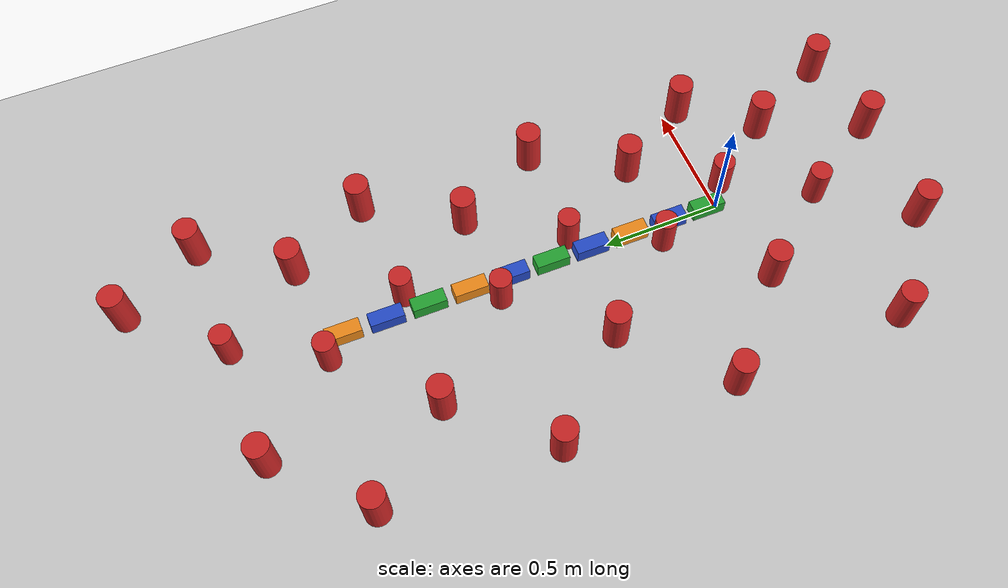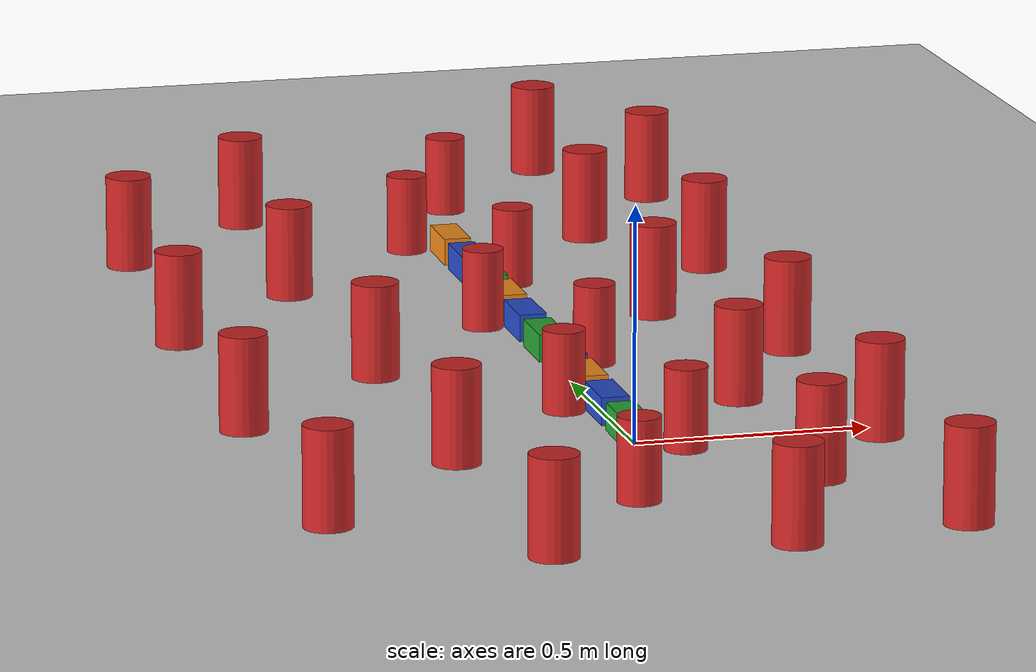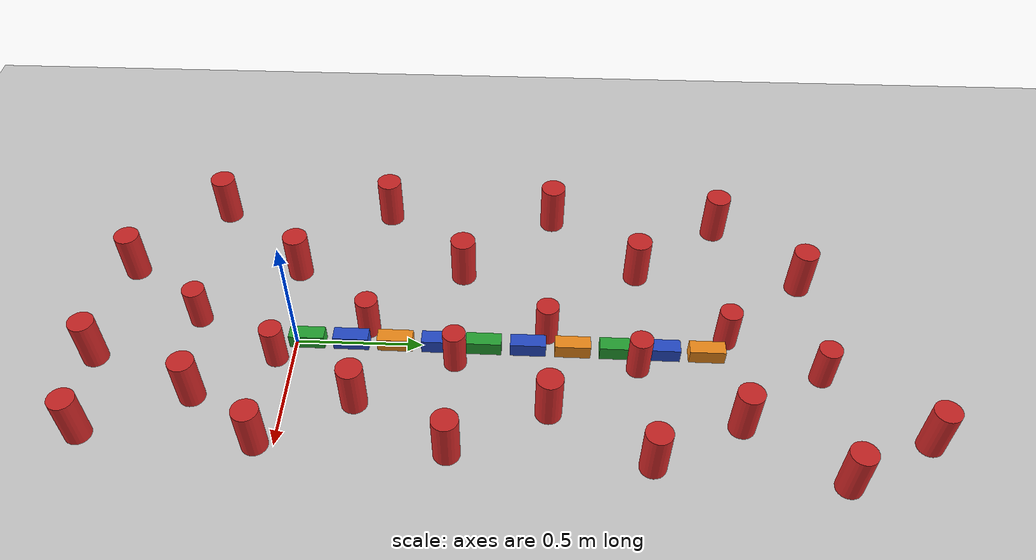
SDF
<sdf version="1.7">
 <world name="default">
  <light name="sun" type="directional">
   <pose>0 0 10 0 -0 0</pose>
   <diffuse>0.8 0.8 0.8 1</diffuse>
   <specular>0.2 0.2 0.2 1</specular>
   <attenuation>
    <range>1000</range>
    <constant>0.9</constant>
    <linear>0.01</linear>
    <quadratic>0.001</quadratic>
   </attenuation>
   <direction>-0.5 0.1 -0.9</direction>
   <spot><inner_angle>0</inner_angle><outer_angle>0</outer_angle><falloff>0</falloff></spot>
  </light>
  <model name="ground_plane">
   <static>1</static>
   <link name="link">
    <collision name="collision">
     <geometry><plane><normal>0 0 1</normal><size>100 100</size></plane></geometry>
     <surface>
      <contact><collide_bitmask>65535</collide_bitmask></contact>
      <friction><ode><mu>100</mu><mu2>50</mu2></ode></friction>
     </surface>
    </collision>
    <visual name="visual">
     <cast_shadows>0</cast_shadows>
     <geometry><plane><normal>0 0 1</normal><size>100 100</size></plane></geometry>
     <material>
      <script><uri>file://media/materials/scripts/gazebo.material</uri><name>Gazebo/Grey</name></script>
     </material>
    </visual>
   </link>
  </model>
  <gravity>0 0 -9.8</gravity>
  <magnetic_field>6e-06 2.3e-05 -4.2e-05</magnetic_field>
  <atmosphere type="adiabatic"/>
  <physics type="ode">
   <max_step_size>0.001</max_step_size>
   <real_time_factor>1</real_time_factor>
   <real_time_update_rate>1000</real_time_update_rate>
  </physics>
  <scene><ambient>0.4 0.4 0.4 1</ambient><background>0.7 0.7 0.7 1</background><shadows>1</shadows></scene>
  <audio><device>default</device></audio>
  <spherical_coordinates>
   <surface_model>EARTH_WGS84</surface_model>
   <latitude_deg>0</latitude_deg>
   <longitude_deg>0</longitude_deg>
   <elevation>0</elevation>
   <heading_deg>0</heading_deg>
  </spherical_coordinates>
  <model name="my_bot">
   <link name="base_link">
    <inertial>
     <pose>0 0.07 0.03 0 -0 0</pose>
     <mass>1</mass>
     <inertia>
      <ixx>0.00193333</ixx>
      <ixy>0</ixy>
      <ixz>0</ixz>
      <iyy>0.0006</iyy>
      <iyz>0</iyz>
      <izz>0.00193333</izz>
     </inertia>
    </inertial>
    <collision name="base_link_fixed_joint_lump__link_1_collision">
     <pose>0 0.07 0.03 0 -0 0</pose>
     <geometry><box><size>0.06 0.14 0.06</size></box></geometry>
    </collision>
    <visual name="base_link_fixed_joint_lump__link_1_visual">
     <pose>0 0.07 0.03 0 -0 0</pose>
     <geometry><box><size>0.06 0.14 0.06</size></box></geometry>
     <material>
      <script><name>Gazebo/Green</name><uri>file://media/materials/scripts/gazebo.material</uri></script>
     </material>
    </visual>
    <visual name="base_link_fixed_joint_lump__camera_link_visual_1">
     <pose>0 0 0.03 0 0 -1.5708</pose>
     <geometry><box><size>0.01 0.01 0.01</size></box></geometry>
     <material>
      <script><name>Gazebo/Red</name><uri>file://media/materials/scripts/gazebo.material</uri></script>
     </material>
    </visual>
    <sensor name="camera" type="camera">
     <visualize>1</visualize>
     <update_rate>10</update_rate>
     <camera>
      <horizontal_fov>1.089</horizontal_fov>
      <image><format>R8G8B8</format><width>640</width><height>480</height></image>
      <clip><near>0.05</near><far>8</far></clip>
     </camera>
     <plugin name="camera_controller" filename="libgazebo_ros_camera.so">
      <frame_name>camera_link_optical</frame_name>
     </plugin>
     <pose>0 0 0.03 0 0 -1.5708</pose>
    </sensor>
   </link>
   <joint name="link_1_2_joint" type="revolute">
    <pose relative_to="base_link">0 0.175 0 0 -0 0</pose>
    <parent>base_link</parent>
    <child>link_2</child>
    <axis>
     <xyz>0 0 1</xyz>
     <limit><lower>-0.785398</lower><upper>0.785398</upper><effort>1000</effort><velocity>50</velocity></limit>
     <dynamics><spring_reference>0</spring_reference><spring_stiffness>0</spring_stiffness></dynamics>
    </axis>
   </joint>
   <link name="link_2">
    <pose relative_to="link_1_2_joint">0 0 0 0 -0 0</pose>
    <inertial>
     <pose>0 0.07 0.03 0 -0 0</pose>
     <mass>1</mass>
     <inertia>
      <ixx>0.00193333</ixx>
      <ixy>0</ixy>
      <ixz>0</ixz>
      <iyy>0.0006</iyy>
      <iyz>0</iyz>
      <izz>0.00193333</izz>
     </inertia>
    </inertial>
    <collision name="link_2_collision">
     <pose>0 0.07 0.03 0 -0 0</pose>
     <geometry><box><size>0.06 0.14 0.06</size></box></geometry>
    </collision>
    <visual name="link_2_visual">
     <pose>0 0.07 0.03 0 -0 0</pose>
     <geometry><box><size>0.06 0.14 0.06</size></box></geometry>
     <material>
      <script><name>Gazebo/Blue</name><uri>file://media/materials/scripts/gazebo.material</uri></script>
     </material>
    </visual>
   </link>
   <joint name="link_2_3_joint" type="revolute">
    <pose relative_to="link_2">0 0.175 0 0 -0 0</pose>
    <parent>link_2</parent>
    <child>link_3</child>
    <axis>
     <xyz>0 0 1</xyz>
     <limit><lower>-0.785398</lower><upper>0.785398</upper><effort>1000</effort><velocity>50</velocity></limit>
     <dynamics><spring_reference>0</spring_reference><spring_stiffness>0</spring_stiffness></dynamics>
    </axis>
   </joint>
   <link name="link_3">
    <pose relative_to="link_2_3_joint">0 0 0 0 -0 0</pose>
    <inertial>
     <pose>0 0.07 0.03 0 -0 0</pose>
     <mass>1</mass>
     <inertia>
      <ixx>0.00193333</ixx>
      <ixy>0</ixy>
      <ixz>0</ixz>
      <iyy>0.0006</iyy>
      <iyz>0</iyz>
      <izz>0.00193333</izz>
     </inertia>
    </inertial>
    <collision name="link_3_collision">
     <pose>0 0.07 0.03 0 -0 0</pose>
     <geometry><box><size>0.06 0.14 0.06</size></box></geometry>
    </collision>
    <visual name="link_3_visual">
     <pose>0 0.07 0.03 0 -0 0</pose>
     <geometry><box><size>0.06 0.14 0.06</size></box></geometry>
     <material>
      <script><name>Gazebo/Orange</name><uri>file://media/materials/scripts/gazebo.material</uri></script>
     </material>
    </visual>
   </link>
   <joint name="link_3_4_joint" type="revolute">
    <pose relative_to="link_3">0 0.175 0 0 -0 0</pose>
    <parent>link_3</parent>
    <child>link_4</child>
    <axis>
     <xyz>0 0 1</xyz>
     <limit><lower>-0.785398</lower><upper>0.785398</upper><effort>1000</effort><velocity>50</velocity></limit>
     <dynamics><spring_reference>0</spring_reference><spring_stiffness>0</spring_stiffness></dynamics>
    </axis>
   </joint>
   <link name="link_4">
    <pose relative_to="link_3_4_joint">0 0 0 0 -0 0</pose>
    <inertial>
     <pose>0 0.07 0.03 0 -0 0</pose>
     <mass>1</mass>
     <inertia>
      <ixx>0.00193333</ixx>
      <ixy>0</ixy>
      <ixz>0</ixz>
      <iyy>0.0006</iyy>
      <iyz>0</iyz>
      <izz>0.00193333</izz>
     </inertia>
    </inertial>
    <collision name="link_4_collision">
     <pose>0 0.07 0.03 0 -0 0</pose>
     <geometry><box><size>0.06 0.14 0.06</size></box></geometry>
    </collision>
    <visual name="link_4_visual">
     <pose>0 0.07 0.03 0 -0 0</pose>
     <geometry><box><size>0.06 0.14 0.06</size></box></geometry>
     <material>
      <script><name>Gazebo/Blue</name><uri>file://media/materials/scripts/gazebo.material</uri></script>
     </material>
    </visual>
   </link>
   <joint name="link_4_5_joint" type="revolute">
    <pose relative_to="link_4">0 0.175 0 0 -0 0</pose>
    <parent>link_4</parent>
    <child>link_5</child>
    <axis>
     <xyz>0 0 1</xyz>
     <limit><lower>-0.785398</lower><upper>0.785398</upper><effort>1000</effort><velocity>50</velocity></limit>
     <dynamics><spring_reference>0</spring_reference><spring_stiffness>0</spring_stiffness></dynamics>
    </axis>
   </joint>
   <link name="link_5">
    <pose relative_to="link_4_5_joint">0 0 0 0 -0 0</pose>
    <inertial>
     <pose>0 0.07 0.03 0 -0 0</pose>
     <mass>1</mass>
     <inertia>
      <ixx>0.00193333</ixx>
      <ixy>0</ixy>
      <ixz>0</ixz>
      <iyy>0.0006</iyy>
      <iyz>0</iyz>
      <izz>0.00193333</izz>
     </inertia>
    </inertial>
    <collision name="link_5_collision">
     <pose>0 0.07 0.03 0 -0 0</pose>
     <geometry><box><size>0.06 0.14 0.06</size></box></geometry>
    </collision>
    <visual name="link_5_visual">
     <pose>0 0.07 0.03 0 -0 0</pose>
     <geometry><box><size>0.06 0.14 0.06</size></box></geometry>
     <material>
      <script><name>Gazebo/Green</name><uri>file://media/materials/scripts/gazebo.material</uri></script>
     </material>
    </visual>
   </link>
   <joint name="link_5_6_joint" type="revolute">
    <pose relative_to="link_5">0 0.175 0 0 -0 0</pose>
    <parent>link_5</parent>
    <child>link_6</child>
    <axis>
     <xyz>0 0 1</xyz>
     <limit><lower>-0.785398</lower><upper>0.785398</upper><effort>1000</effort><velocity>50</velocity></limit>
     <dynamics><spring_reference>0</spring_reference><spring_stiffness>0</spring_stiffness></dynamics>
    </axis>
   </joint>
   <link name="link_6">
    <pose relative_to="link_5_6_joint">0 0 0 0 -0 0</pose>
    <inertial>
     <pose>0 0.07 0.03 0 -0 0</pose>
     <mass>1</mass>
     <inertia>
      <ixx>0.00193333</ixx>
      <ixy>0</ixy>
      <ixz>0</ixz>
      <iyy>0.0006</iyy>
      <iyz>0</iyz>
      <izz>0.00193333</izz>
     </inertia>
    </inertial>
    <collision name="link_6_collision">
     <pose>0 0.07 0.03 0 -0 0</pose>
     <geometry><box><size>0.06 0.14 0.06</size></box></geometry>
    </collision>
    <visual name="link_6_visual">
     <pose>0 0.07 0.03 0 -0 0</pose>
     <geometry><box><size>0.06 0.14 0.06</size></box></geometry>
     <material>
      <script><name>Gazebo/Blue</name><uri>file://media/materials/scripts/gazebo.material</uri></script>
     </material>
    </visual>
   </link>
   <joint name="link_6_7_joint" type="revolute">
    <pose relative_to="link_6">0 0.175 0 0 -0 0</pose>
    <parent>link_6</parent>
    <child>link_7</child>
    <axis>
     <xyz>0 0 1</xyz>
     <limit><lower>-0.785398</lower><upper>0.785398</upper><effort>1000</effort><velocity>50</velocity></limit>
     <dynamics><spring_reference>0</spring_reference><spring_stiffness>0</spring_stiffness></dynamics>
    </axis>
   </joint>
   <link name="link_7">
    <pose relative_to="link_6_7_joint">0 0 0 0 -0 0</pose>
    <inertial>
     <pose>0 0.07 0.03 0 -0 0</pose>
     <mass>1</mass>
     <inertia>
      <ixx>0.00193333</ixx>
      <ixy>0</ixy>
      <ixz>0</ixz>
      <iyy>0.0006</iyy>
      <iyz>0</iyz>
      <izz>0.00193333</izz>
     </inertia>
    </inertial>
    <collision name="link_7_collision">
     <pose>0 0.07 0.03 0 -0 0</pose>
     <geometry><box><size>0.06 0.14 0.06</size></box></geometry>
    </collision>
    <visual name="link_7_visual">
     <pose>0 0.07 0.03 0 -0 0</pose>
     <geometry><box><size>0.06 0.14 0.06</size></box></geometry>
     <material>
      <script><name>Gazebo/Orange</name><uri>file://media/materials/scripts/gazebo.material</uri></script>
     </material>
    </visual>
   </link>
   <joint name="link_7_8_joint" type="revolute">
    <pose relative_to="link_7">0 0.175 0 0 -0 0</pose>
    <parent>link_7</parent>
    <child>link_8</child>
    <axis>
     <xyz>0 0 1</xyz>
     <limit><lower>-0.785398</lower><upper>0.785398</upper><effort>1000</effort><velocity>50</velocity></limit>
     <dynamics><spring_reference>0</spring_reference><spring_stiffness>0</spring_stiffness></dynamics>
    </axis>
   </joint>
   <link name="link_8">
    <pose relative_to="link_7_8_joint">0 0 0 0 -0 0</pose>
    <inertial>
     <pose>0 0.07 0.03 0 -0 0</pose>
     <mass>1</mass>
     <inertia>
      <ixx>0.00193333</ixx>
      <ixy>0</ixy>
      <ixz>0</ixz>
      <iyy>0.0006</iyy>
      <iyz>0</iyz>
      <izz>0.00193333</izz>
     </inertia>
    </inertial>
    <collision name="link_8_collision">
     <pose>0 0.07 0.03 0 -0 0</pose>
     <geometry><box><size>0.06 0.14 0.06</size></box></geometry>
    </collision>
    <visual name="link_8_visual">
     <pose>0 0.07 0.03 0 -0 0</pose>
     <geometry><box><size>0.06 0.14 0.06</size></box></geometry>
     <material>
      <script><name>Gazebo/Green</name><uri>file://media/materials/scripts/gazebo.material</uri></script>
     </material>
    </visual>
   </link>
   <joint name="link_8_9_joint" type="revolute">
    <pose relative_to="link_8">0 0.175 0 0 -0 0</pose>
    <parent>link_8</parent>
    <child>link_9</child>
    <axis>
     <xyz>0 0 1</xyz>
     <limit><lower>-0.785398</lower><upper>0.785398</upper><effort>1000</effort><velocity>50</velocity></limit>
     <dynamics><spring_reference>0</spring_reference><spring_stiffness>0</spring_stiffness></dynamics>
    </axis>
   </joint>
   <link name="link_9">
    <pose relative_to="link_8_9_joint">0 0 0 0 -0 0</pose>
    <inertial>
     <pose>0 0.07 0.03 0 -0 0</pose>
     <mass>1</mass>
     <inertia>
      <ixx>0.00193333</ixx>
      <ixy>0</ixy>
      <ixz>0</ixz>
      <iyy>0.0006</iyy>
      <iyz>0</iyz>
      <izz>0.00193333</izz>
     </inertia>
    </inertial>
    <collision name="link_9_collision">
     <pose>0 0.07 0.03 0 -0 0</pose>
     <geometry><box><size>0.06 0.14 0.06</size></box></geometry>
    </collision>
    <visual name="link_9_visual">
     <pose>0 0.07 0.03 0 -0 0</pose>
     <geometry><box><size>0.06 0.14 0.06</size></box></geometry>
     <material>
      <script><name>Gazebo/Blue</name><uri>file://media/materials/scripts/gazebo.material</uri></script>
     </material>
    </visual>
   </link>
   <joint name="link_9_10_joint" type="revolute">
    <pose relative_to="link_9">0 0.175 0 0 -0 0</pose>
    <parent>link_9</parent>
    <child>link_10</child>
    <axis>
     <xyz>0 0 1</xyz>
     <limit><lower>-0.785398</lower><upper>0.785398</upper><effort>1000</effort><velocity>50</velocity></limit>
     <dynamics><spring_reference>0</spring_reference><spring_stiffness>0</spring_stiffness></dynamics>
    </axis>
   </joint>
   <link name="link_10">
    <pose relative_to="link_9_10_joint">0 0 0 0 -0 0</pose>
    <inertial>
     <pose>0 0.07 0.03 0 -0 0</pose>
     <mass>1</mass>
     <inertia>
      <ixx>0.00193333</ixx>
      <ixy>0</ixy>
      <ixz>0</ixz>
      <iyy>0.0006</iyy>
      <iyz>0</iyz>
      <izz>0.00193333</izz>
     </inertia>
    </inertial>
    <collision name="link_10_collision">
     <pose>0 0.07 0.03 0 -0 0</pose>
     <geometry><box><size>0.06 0.14 0.06</size></box></geometry>
    </collision>
    <visual name="link_10_visual">
     <pose>0 0.07 0.03 0 -0 0</pose>
     <geometry><box><size>0.06 0.14 0.06</size></box></geometry>
     <material>
      <script><name>Gazebo/Orange</name><uri>file://media/materials/scripts/gazebo.material</uri></script>
     </material>
    </visual>
   </link>
   <static>0</static>
   <plugin name="gazebo_ros_planar_move" filename="libgazebo_ros_planar_move.so">
    <update_rate>100</update_rate>
    <publish_rate>10</publish_rate>
    <publish_odom>1</publish_odom>
    <publish_odom_tf>1</publish_odom_tf>
    <odometry_frame>odom</odometry_frame>
    <robot_base_frame>base_link</robot_base_frame>
   </plugin>
   <plugin name="gazebo_ros2_control" filename="libgazebo_ros2_control.so">
    <parameters>/home/mohit/GITHUBRepos/snake-robot-sim/install/snake_bot/share/snake_bot/config/controllers.yaml</parameters>
   </plugin>
   <plugin name="ft_sensor" filename="libgazebo_ros_ft_sensor.so">
    <updateRate>100.0</updateRate>
    <remapping>wrench:=joint_1</remapping>
    <joint_name>link_1_2_joint</joint_name>
    <gaussian_noise>0.01</gaussian_noise>
    <update_rate>1</update_rate>
   </plugin>
   <pose>-0.00067 -0.024849 0 -0 -0 -0.01054</pose>
  </model>
  <model name="model">
   <link name="link_0">
    <inertial>
     <mass>1e+10</mass>
     <inertia>
      <ixx>3.11188e+07</ixx>
      <ixy>0</ixy>
      <ixz>0</ixz>
      <iyy>3.11188e+07</iyy>
      <iyz>0</iyz>
      <izz>1.00639e+07</izz>
     </inertia>
    </inertial>
    <pose>0.081479 -0.882122 0 0 -0 0</pose>
    <visual name="visual">
     <geometry><cylinder><radius>0.0448636</radius><length>0.17693</length></cylinder></geometry>
     <material>
      <lighting>1</lighting>
      <script><uri>file://media/materials/scripts/gazebo.material</uri><name>Gazebo/Red</name></script>
      <shader type="pixel"><normal_map>__default__</normal_map></shader>
      <ambient>1 0 0 1</ambient>
      <diffuse>1 0 0 1</diffuse>
      <specular>0.1 0.1 0.1 1</specular>
      <emissive>0 0 0 1</emissive>
     </material>
    </visual>
    <collision name="collision">
     <geometry><cylinder><radius>0.044864</radius><length>0.17693</length></cylinder></geometry>
     <surface>
      <friction>
       <ode><mu>1</mu><mu2>1</mu2><fdir1>0 0 0</fdir1><slip1>0</slip1><slip2>0</slip2></ode>
       <torsional>
        <coefficient>1</coefficient>
        <patch_radius>0</patch_radius>
        <surface_radius>0</surface_radius>
        <use_patch_radius>1</use_patch_radius>
        <ode><slip>0</slip></ode>
       </torsional>
      </friction>
      <bounce><restitution_coefficient>0</restitution_coefficient><threshold>1e+06</threshold></bounce>
      <contact>
       <collide_without_contact>0</collide_without_contact>
       <collide_without_contact_bitmask>1</collide_without_contact_bitmask>
       <collide_bitmask>1</collide_bitmask>
       <ode>
        <soft_cfm>0</soft_cfm>
        <soft_erp>0.2</soft_erp>
        <kp>1e+13</kp>
        <kd>1</kd>
        <max_vel>0.01</max_vel>
        <min_depth>0</min_depth>
       </ode>
       <bullet>
        <split_impulse>1</split_impulse>
        <split_impulse_penetration_threshold>-0.01</split_impulse_penetration_threshold>
        <soft_cfm>0</soft_cfm>
        <soft_erp>0.2</soft_erp>
        <kp>1e+13</kp>
        <kd>1</kd>
       </bullet>
      </contact>
     </surface>
    </collision>
   </link>
   <link name="link_0_clone">
    <inertial>
     <mass>1e+10</mass>
     <inertia>
      <ixx>3.11188e+07</ixx>
      <ixy>0</ixy>
      <ixz>0</ixz>
      <iyy>3.11188e+07</iyy>
      <iyz>0</iyz>
      <izz>1.00639e+07</izz>
     </inertia>
    </inertial>
    <pose>-0.08293 -0.536122 0 0 -0 0</pose>
    <visual name="visual">
     <geometry><cylinder><radius>0.0448636</radius><length>0.17693</length></cylinder></geometry>
     <material>
      <lighting>1</lighting>
      <script><uri>file://media/materials/scripts/gazebo.material</uri><name>Gazebo/Red</name></script>
      <shader type="pixel"><normal_map>__default__</normal_map></shader>
      <ambient>1 0 0 1</ambient>
      <diffuse>1 0 0 1</diffuse>
      <specular>0.1 0.1 0.1 1</specular>
      <emissive>0 0 0 1</emissive>
     </material>
    </visual>
    <collision name="collision">
     <geometry><cylinder><radius>0.044864</radius><length>0.17693</length></cylinder></geometry>
     <surface>
      <friction>
       <ode><mu>1</mu><mu2>1</mu2><fdir1>0 0 0</fdir1><slip1>0</slip1><slip2>0</slip2></ode>
       <torsional>
        <coefficient>1</coefficient>
        <patch_radius>0</patch_radius>
        <surface_radius>0</surface_radius>
        <use_patch_radius>1</use_patch_radius>
        <ode><slip>0</slip></ode>
       </torsional>
      </friction>
      <bounce><restitution_coefficient>0</restitution_coefficient><threshold>1e+06</threshold></bounce>
      <contact>
       <collide_without_contact>0</collide_without_contact>
       <collide_without_contact_bitmask>1</collide_without_contact_bitmask>
       <collide_bitmask>1</collide_bitmask>
       <ode>
        <soft_cfm>0</soft_cfm>
        <soft_erp>0.2</soft_erp>
        <kp>1e+13</kp>
        <kd>1</kd>
        <max_vel>0.01</max_vel>
        <min_depth>0</min_depth>
       </ode>
       <bullet>
        <split_impulse>1</split_impulse>
        <split_impulse_penetration_threshold>-0.01</split_impulse_penetration_threshold>
        <soft_cfm>0</soft_cfm>
        <soft_erp>0.2</soft_erp>
        <kp>1e+13</kp>
        <kd>1</kd>
       </bullet>
      </contact>
     </surface>
    </collision>
   </link>
   <link name="link_0_clone_0">
    <inertial>
     <mass>1e+10</mass>
     <inertia>
      <ixx>3.11188e+07</ixx>
      <ixy>0</ixy>
      <ixz>0</ixz>
      <iyy>3.11188e+07</iyy>
      <iyz>0</iyz>
      <izz>1.00639e+07</izz>
     </inertia>
    </inertial>
    <pose>0.078553 -0.180553 0 0 -0 0</pose>
    <visual name="visual">
     <geometry><cylinder><radius>0.0448636</radius><length>0.17693</length></cylinder></geometry>
     <material>
      <lighting>1</lighting>
      <script><uri>file://media/materials/scripts/gazebo.material</uri><name>Gazebo/Red</name></script>
      <shader type="pixel"><normal_map>__default__</normal_map></shader>
      <ambient>1 0 0 1</ambient>
      <diffuse>1 0 0 1</diffuse>
      <specular>0.1 0.1 0.1 1</specular>
      <emissive>0 0 0 1</emissive>
     </material>
    </visual>
    <collision name="collision">
     <geometry><cylinder><radius>0.044864</radius><length>0.17693</length></cylinder></geometry>
     <surface>
      <friction>
       <ode><mu>1</mu><mu2>1</mu2><fdir1>0 0 0</fdir1><slip1>0</slip1><slip2>0</slip2></ode>
       <torsional>
        <coefficient>1</coefficient>
        <patch_radius>0</patch_radius>
        <surface_radius>0</surface_radius>
        <use_patch_radius>1</use_patch_radius>
        <ode><slip>0</slip></ode>
       </torsional>
      </friction>
      <bounce><restitution_coefficient>0</restitution_coefficient><threshold>1e+06</threshold></bounce>
      <contact>
       <collide_without_contact>0</collide_without_contact>
       <collide_without_contact_bitmask>1</collide_without_contact_bitmask>
       <collide_bitmask>1</collide_bitmask>
       <ode>
        <soft_cfm>0</soft_cfm>
        <soft_erp>0.2</soft_erp>
        <kp>1e+13</kp>
        <kd>1</kd>
        <max_vel>0.01</max_vel>
        <min_depth>0</min_depth>
       </ode>
       <bullet>
        <split_impulse>1</split_impulse>
        <split_impulse_penetration_threshold>-0.01</split_impulse_penetration_threshold>
        <soft_cfm>0</soft_cfm>
        <soft_erp>0.2</soft_erp>
        <kp>1e+13</kp>
        <kd>1</kd>
       </bullet>
      </contact>
     </surface>
    </collision>
   </link>
   <link name="link_0_clone_1">
    <inertial>
     <mass>1e+10</mass>
     <inertia>
      <ixx>3.11188e+07</ixx>
      <ixy>0</ixy>
      <ixz>0</ixz>
      <iyy>3.11188e+07</iyy>
      <iyz>0</iyz>
      <izz>1.00639e+07</izz>
     </inertia>
    </inertial>
    <pose>-0.076096 0.175363 0 0 -0 0</pose>
    <visual name="visual">
     <geometry><cylinder><radius>0.0448636</radius><length>0.17693</length></cylinder></geometry>
     <material>
      <lighting>1</lighting>
      <script><uri>file://media/materials/scripts/gazebo.material</uri><name>Gazebo/Red</name></script>
      <shader type="pixel"><normal_map>__default__</normal_map></shader>
      <ambient>1 0 0 1</ambient>
      <diffuse>1 0 0 1</diffuse>
      <specular>0.1 0.1 0.1 1</specular>
      <emissive>0 0 0 1</emissive>
     </material>
    </visual>
    <collision name="collision">
     <geometry><cylinder><radius>0.044864</radius><length>0.17693</length></cylinder></geometry>
     <surface>
      <friction>
       <ode><mu>1</mu><mu2>1</mu2><fdir1>0 0 0</fdir1><slip1>0</slip1><slip2>0</slip2></ode>
       <torsional>
        <coefficient>1</coefficient>
        <patch_radius>0</patch_radius>
        <surface_radius>0</surface_radius>
        <use_patch_radius>1</use_patch_radius>
        <ode><slip>0</slip></ode>
       </torsional>
      </friction>
      <bounce><restitution_coefficient>0</restitution_coefficient><threshold>1e+06</threshold></bounce>
      <contact>
       <collide_without_contact>0</collide_without_contact>
       <collide_without_contact_bitmask>1</collide_without_contact_bitmask>
       <collide_bitmask>1</collide_bitmask>
       <ode>
        <soft_cfm>0</soft_cfm>
        <soft_erp>0.2</soft_erp>
        <kp>1e+13</kp>
        <kd>1</kd>
        <max_vel>0.01</max_vel>
        <min_depth>0</min_depth>
       </ode>
       <bullet>
        <split_impulse>1</split_impulse>
        <split_impulse_penetration_threshold>-0.01</split_impulse_penetration_threshold>
        <soft_cfm>0</soft_cfm>
        <soft_erp>0.2</soft_erp>
        <kp>1e+13</kp>
        <kd>1</kd>
       </bullet>
      </contact>
     </surface>
    </collision>
   </link>
   <link name="link_0_clone_1_clone">
    <inertial>
     <mass>1e+10</mass>
     <inertia>
      <ixx>3.11188e+07</ixx>
      <ixy>0</ixy>
      <ixz>0</ixz>
      <iyy>3.11188e+07</iyy>
      <iyz>0</iyz>
      <izz>1.00639e+07</izz>
     </inertia>
    </inertial>
    <pose>0.08216 0.531048 0 0 -0 0</pose>
    <visual name="visual">
     <geometry><cylinder><radius>0.0448636</radius><length>0.17693</length></cylinder></geometry>
     <material>
      <lighting>1</lighting>
      <script><uri>file://media/materials/scripts/gazebo.material</uri><name>Gazebo/Red</name></script>
      <shader type="pixel"><normal_map>__default__</normal_map></shader>
      <ambient>1 0 0 1</ambient>
      <diffuse>1 0 0 1</diffuse>
      <specular>0.1 0.1 0.1 1</specular>
      <emissive>0 0 0 1</emissive>
     </material>
    </visual>
    <collision name="collision">
     <geometry><cylinder><radius>0.044864</radius><length>0.17693</length></cylinder></geometry>
     <surface>
      <friction>
       <ode><mu>1</mu><mu2>1</mu2><fdir1>0 0 0</fdir1><slip1>0</slip1><slip2>0</slip2></ode>
       <torsional>
        <coefficient>1</coefficient>
        <patch_radius>0</patch_radius>
        <surface_radius>0</surface_radius>
        <use_patch_radius>1</use_patch_radius>
        <ode><slip>0</slip></ode>
       </torsional>
      </friction>
      <bounce><restitution_coefficient>0</restitution_coefficient><threshold>1e+06</threshold></bounce>
      <contact>
       <collide_without_contact>0</collide_without_contact>
       <collide_without_contact_bitmask>1</collide_without_contact_bitmask>
       <collide_bitmask>1</collide_bitmask>
       <ode>
        <soft_cfm>0</soft_cfm>
        <soft_erp>0.2</soft_erp>
        <kp>1e+13</kp>
        <kd>1</kd>
        <max_vel>0.01</max_vel>
        <min_depth>0</min_depth>
       </ode>
       <bullet>
        <split_impulse>1</split_impulse>
        <split_impulse_penetration_threshold>-0.01</split_impulse_penetration_threshold>
        <soft_cfm>0</soft_cfm>
        <soft_erp>0.2</soft_erp>
        <kp>1e+13</kp>
        <kd>1</kd>
       </bullet>
      </contact>
     </surface>
    </collision>
   </link>
   <link name="link_0_clone_1_clone_0">
    <inertial>
     <mass>1e+10</mass>
     <inertia>
      <ixx>3.11188e+07</ixx>
      <ixy>0</ixy>
      <ixz>0</ixz>
      <iyy>3.11188e+07</iyy>
      <iyz>0</iyz>
      <izz>1.00639e+07</izz>
     </inertia>
    </inertial>
    <pose>-0.073268 0.8857 0 0 -0 0</pose>
    <visual name="visual">
     <geometry><cylinder><radius>0.0448636</radius><length>0.17693</length></cylinder></geometry>
     <material>
      <lighting>1</lighting>
      <script><uri>file://media/materials/scripts/gazebo.material</uri><name>Gazebo/Red</name></script>
      <shader type="pixel"><normal_map>__default__</normal_map></shader>
      <ambient>1 0 0 1</ambient>
      <diffuse>1 0 0 1</diffuse>
      <specular>0.1 0.1 0.1 1</specular>
      <emissive>0 0 0 1</emissive>
     </material>
    </visual>
    <collision name="collision">
     <geometry><cylinder><radius>0.044864</radius><length>0.17693</length></cylinder></geometry>
     <surface>
      <friction>
       <ode><mu>1</mu><mu2>1</mu2><fdir1>0 0 0</fdir1><slip1>0</slip1><slip2>0</slip2></ode>
       <torsional>
        <coefficient>1</coefficient>
        <patch_radius>0</patch_radius>
        <surface_radius>0</surface_radius>
        <use_patch_radius>1</use_patch_radius>
        <ode><slip>0</slip></ode>
       </torsional>
      </friction>
      <bounce><restitution_coefficient>0</restitution_coefficient><threshold>1e+06</threshold></bounce>
      <contact>
       <collide_without_contact>0</collide_without_contact>
       <collide_without_contact_bitmask>1</collide_without_contact_bitmask>
       <collide_bitmask>1</collide_bitmask>
       <ode>
        <soft_cfm>0</soft_cfm>
        <soft_erp>0.2</soft_erp>
        <kp>1e+13</kp>
        <kd>1</kd>
        <max_vel>0.01</max_vel>
        <min_depth>0</min_depth>
       </ode>
       <bullet>
        <split_impulse>1</split_impulse>
        <split_impulse_penetration_threshold>-0.01</split_impulse_penetration_threshold>
        <soft_cfm>0</soft_cfm>
        <soft_erp>0.2</soft_erp>
        <kp>1e+13</kp>
        <kd>1</kd>
       </bullet>
      </contact>
     </surface>
    </collision>
   </link>
   <link name="link_0_clone_1_clone_1">
    <inertial>
     <mass>1e+10</mass>
     <inertia>
      <ixx>3.11188e+07</ixx>
      <ixy>0</ixy>
      <ixz>0</ixz>
      <iyy>3.11188e+07</iyy>
      <iyz>0</iyz>
      <izz>1.00639e+07</izz>
     </inertia>
    </inertial>
    <pose>0.102666 1.23379 0 0 -0 0</pose>
    <visual name="visual">
     <geometry><cylinder><radius>0.0448636</radius><length>0.17693</length></cylinder></geometry>
     <material>
      <lighting>1</lighting>
      <script><uri>file://media/materials/scripts/gazebo.material</uri><name>Gazebo/Red</name></script>
      <shader type="pixel"><normal_map>__default__</normal_map></shader>
      <ambient>1 0 0 1</ambient>
      <diffuse>1 0 0 1</diffuse>
      <specular>0.1 0.1 0.1 1</specular>
      <emissive>0 0 0 1</emissive>
     </material>
    </visual>
    <collision name="collision">
     <geometry><cylinder><radius>0.044864</radius><length>0.17693</length></cylinder></geometry>
     <surface>
      <friction>
       <ode><mu>1</mu><mu2>1</mu2><fdir1>0 0 0</fdir1><slip1>0</slip1><slip2>0</slip2></ode>
       <torsional>
        <coefficient>1</coefficient>
        <patch_radius>0</patch_radius>
        <surface_radius>0</surface_radius>
        <use_patch_radius>1</use_patch_radius>
        <ode><slip>0</slip></ode>
       </torsional>
      </friction>
      <bounce><restitution_coefficient>0</restitution_coefficient><threshold>1e+06</threshold></bounce>
      <contact>
       <collide_without_contact>0</collide_without_contact>
       <collide_without_contact_bitmask>1</collide_without_contact_bitmask>
       <collide_bitmask>1</collide_bitmask>
       <ode>
        <soft_cfm>0</soft_cfm>
        <soft_erp>0.2</soft_erp>
        <kp>1e+13</kp>
        <kd>1</kd>
        <max_vel>0.01</max_vel>
        <min_depth>0</min_depth>
       </ode>
       <bullet>
        <split_impulse>1</split_impulse>
        <split_impulse_penetration_threshold>-0.01</split_impulse_penetration_threshold>
        <soft_cfm>0</soft_cfm>
        <soft_erp>0.2</soft_erp>
        <kp>1e+13</kp>
        <kd>1</kd>
       </bullet>
      </contact>
     </surface>
    </collision>
   </link>
   <link name="link_0_clone_2">
    <inertial>
     <mass>1e+10</mass>
     <inertia>
      <ixx>3.11188e+07</ixx>
      <ixy>0</ixy>
      <ixz>0</ixz>
      <iyy>3.11188e+07</iyy>
      <iyz>0</iyz>
      <izz>1.00639e+07</izz>
     </inertia>
    </inertial>
    <pose>-0.112564 -1.2271 0 0 -0 0</pose>
    <visual name="visual">
     <geometry><cylinder><radius>0.0448636</radius><length>0.17693</length></cylinder></geometry>
     <material>
      <lighting>1</lighting>
      <script><uri>file://media/materials/scripts/gazebo.material</uri><name>Gazebo/Red</name></script>
      <shader type="pixel"><normal_map>__default__</normal_map></shader>
      <ambient>1 0 0 1</ambient>
      <diffuse>1 0 0 1</diffuse>
      <specular>0.1 0.1 0.1 1</specular>
      <emissive>0 0 0 1</emissive>
     </material>
    </visual>
    <collision name="collision">
     <geometry><cylinder><radius>0.044864</radius><length>0.17693</length></cylinder></geometry>
     <surface>
      <friction>
       <ode><mu>1</mu><mu2>1</mu2><fdir1>0 0 0</fdir1><slip1>0</slip1><slip2>0</slip2></ode>
       <torsional>
        <coefficient>1</coefficient>
        <patch_radius>0</patch_radius>
        <surface_radius>0</surface_radius>
        <use_patch_radius>1</use_patch_radius>
        <ode><slip>0</slip></ode>
       </torsional>
      </friction>
      <bounce><restitution_coefficient>0</restitution_coefficient><threshold>1e+06</threshold></bounce>
      <contact>
       <collide_without_contact>0</collide_without_contact>
       <collide_without_contact_bitmask>1</collide_without_contact_bitmask>
       <collide_bitmask>1</collide_bitmask>
       <ode>
        <soft_cfm>0</soft_cfm>
        <soft_erp>0.2</soft_erp>
        <kp>1e+13</kp>
        <kd>1</kd>
        <max_vel>0.01</max_vel>
        <min_depth>0</min_depth>
       </ode>
       <bullet>
        <split_impulse>1</split_impulse>
        <split_impulse_penetration_threshold>-0.01</split_impulse_penetration_threshold>
        <soft_cfm>0</soft_cfm>
        <soft_erp>0.2</soft_erp>
        <kp>1e+13</kp>
        <kd>1</kd>
       </bullet>
      </contact>
     </surface>
    </collision>
   </link>
   <static>1</static>
   <pose>0.008468 0.817097 0.088981 0 -0 0</pose>
  </model>
  <model name="static2">
   <link name="link_0">
    <inertial>
     <mass>0.00215539</mass>
     <inertia>
      <ixx>9.22e-06</ixx>
      <ixy>0</ixy>
      <ixz>0</ixz>
      <iyy>9.22e-06</iyy>
      <iyz>0</iyz>
      <izz>2.78e-06</izz>
     </inertia>
    </inertial>
    <pose>0.341007 0.332546 -0 0 -0 0</pose>
    <visual name="visual">
     <geometry><cylinder><radius>0.0508338</radius><length>0.208743</length></cylinder></geometry>
     <material>
      <lighting>1</lighting>
      <script><uri>file://media/materials/scripts/gazebo.material</uri><name>Gazebo/Red</name></script>
      <shader type="pixel"><normal_map>__default__</normal_map></shader>
      <ambient>1 0 0 1</ambient>
      <diffuse>1 0 0 1</diffuse>
      <specular>0.1 0.1 0.1 1</specular>
      <emissive>0 0 0 1</emissive>
     </material>
    </visual>
    <collision name="collision">
     <geometry><cylinder><radius>0.050834</radius><length>0.208743</length></cylinder></geometry>
     <surface>
      <friction>
       <ode><mu>1</mu><mu2>1</mu2><fdir1>0 0 0</fdir1><slip1>0</slip1><slip2>0</slip2></ode>
       <torsional>
        <coefficient>1</coefficient>
        <patch_radius>0</patch_radius>
        <surface_radius>0</surface_radius>
        <use_patch_radius>1</use_patch_radius>
        <ode><slip>0</slip></ode>
       </torsional>
      </friction>
      <bounce><restitution_coefficient>0</restitution_coefficient><threshold>1e+06</threshold></bounce>
      <contact>
       <collide_without_contact>0</collide_without_contact>
       <collide_without_contact_bitmask>1</collide_without_contact_bitmask>
       <collide_bitmask>1</collide_bitmask>
       <ode>
        <soft_cfm>0</soft_cfm>
        <soft_erp>0.2</soft_erp>
        <kp>1e+13</kp>
        <kd>1</kd>
        <max_vel>0.01</max_vel>
        <min_depth>0</min_depth>
       </ode>
       <bullet>
        <split_impulse>1</split_impulse>
        <split_impulse_penetration_threshold>-0.01</split_impulse_penetration_threshold>
        <soft_cfm>0</soft_cfm>
        <soft_erp>0.2</soft_erp>
        <kp>1e+13</kp>
        <kd>1</kd>
       </bullet>
      </contact>
     </surface>
    </collision>
   </link>
   <link name="link_0_clone">
    <inertial>
     <mass>0.00215539</mass>
     <inertia>
      <ixx>9.22e-06</ixx>
      <ixy>0</ixy>
      <ixz>0</ixz>
      <iyy>9.22e-06</iyy>
      <iyz>0</iyz>
      <izz>2.78e-06</izz>
     </inertia>
    </inertial>
    <pose>0.321309 -0.399135 -0 0 -0 0</pose>
    <visual name="visual">
     <geometry><cylinder><radius>0.0508338</radius><length>0.208743</length></cylinder></geometry>
     <material>
      <lighting>1</lighting>
      <script><uri>file://media/materials/scripts/gazebo.material</uri><name>Gazebo/Red</name></script>
      <shader type="pixel"><normal_map>__default__</normal_map></shader>
      <ambient>1 0 0 1</ambient>
      <diffuse>1 0 0 1</diffuse>
      <specular>0.1 0.1 0.1 1</specular>
      <emissive>0 0 0 1</emissive>
     </material>
    </visual>
    <collision name="collision">
     <geometry><cylinder><radius>0.050834</radius><length>0.208743</length></cylinder></geometry>
     <surface>
      <friction>
       <ode><mu>1</mu><mu2>1</mu2><fdir1>0 0 0</fdir1><slip1>0</slip1><slip2>0</slip2></ode>
       <torsional>
        <coefficient>1</coefficient>
        <patch_radius>0</patch_radius>
        <surface_radius>0</surface_radius>
        <use_patch_radius>1</use_patch_radius>
        <ode><slip>0</slip></ode>
       </torsional>
      </friction>
      <bounce><restitution_coefficient>0</restitution_coefficient><threshold>1e+06</threshold></bounce>
      <contact>
       <collide_without_contact>0</collide_without_contact>
       <collide_without_contact_bitmask>1</collide_without_contact_bitmask>
       <collide_bitmask>1</collide_bitmask>
       <ode>
        <soft_cfm>0</soft_cfm>
        <soft_erp>0.2</soft_erp>
        <kp>1e+13</kp>
        <kd>1</kd>
        <max_vel>0.01</max_vel>
        <min_depth>0</min_depth>
       </ode>
       <bullet>
        <split_impulse>1</split_impulse>
        <split_impulse_penetration_threshold>-0.01</split_impulse_penetration_threshold>
        <soft_cfm>0</soft_cfm>
        <soft_erp>0.2</soft_erp>
        <kp>1e+13</kp>
        <kd>1</kd>
       </bullet>
      </contact>
     </surface>
    </collision>
   </link>
   <link name="link_0_clone_0">
    <inertial>
     <mass>0.00215539</mass>
     <inertia>
      <ixx>9.22e-06</ixx>
      <ixy>0</ixy>
      <ixz>0</ixz>
      <iyy>9.22e-06</iyy>
      <iyz>0</iyz>
      <izz>2.78e-06</izz>
     </inertia>
    </inertial>
    <pose>0.537186 -0.03451 -0 0 -0 0</pose>
    <visual name="visual">
     <geometry><cylinder><radius>0.0508338</radius><length>0.208743</length></cylinder></geometry>
     <material>
      <lighting>1</lighting>
      <script><uri>file://media/materials/scripts/gazebo.material</uri><name>Gazebo/Red</name></script>
      <shader type="pixel"><normal_map>__default__</normal_map></shader>
      <ambient>1 0 0 1</ambient>
      <diffuse>1 0 0 1</diffuse>
      <specular>0.1 0.1 0.1 1</specular>
      <emissive>0 0 0 1</emissive>
     </material>
    </visual>
    <collision name="collision">
     <geometry><cylinder><radius>0.050834</radius><length>0.208743</length></cylinder></geometry>
     <surface>
      <friction>
       <ode><mu>1</mu><mu2>1</mu2><fdir1>0 0 0</fdir1><slip1>0</slip1><slip2>0</slip2></ode>
       <torsional>
        <coefficient>1</coefficient>
        <patch_radius>0</patch_radius>
        <surface_radius>0</surface_radius>
        <use_patch_radius>1</use_patch_radius>
        <ode><slip>0</slip></ode>
       </torsional>
      </friction>
      <bounce><restitution_coefficient>0</restitution_coefficient><threshold>1e+06</threshold></bounce>
      <contact>
       <collide_without_contact>0</collide_without_contact>
       <collide_without_contact_bitmask>1</collide_without_contact_bitmask>
       <collide_bitmask>1</collide_bitmask>
       <ode>
        <soft_cfm>0</soft_cfm>
        <soft_erp>0.2</soft_erp>
        <kp>1e+13</kp>
        <kd>1</kd>
        <max_vel>0.01</max_vel>
        <min_depth>0</min_depth>
       </ode>
       <bullet>
        <split_impulse>1</split_impulse>
        <split_impulse_penetration_threshold>-0.01</split_impulse_penetration_threshold>
        <soft_cfm>0</soft_cfm>
        <soft_erp>0.2</soft_erp>
        <kp>1e+13</kp>
        <kd>1</kd>
       </bullet>
      </contact>
     </surface>
    </collision>
   </link>
   <link name="link_0_clone_1">
    <inertial>
     <mass>0.00215539</mass>
     <inertia>
      <ixx>9.22e-06</ixx>
      <ixy>0</ixy>
      <ixz>0</ixz>
      <iyy>9.22e-06</iyy>
      <iyz>0</iyz>
      <izz>2.78e-06</izz>
     </inertia>
    </inertial>
    <pose>0.564834 0.70816 -0 0 -0 0</pose>
    <visual name="visual">
     <geometry><cylinder><radius>0.0508338</radius><length>0.208743</length></cylinder></geometry>
     <material>
      <lighting>1</lighting>
      <script><uri>file://media/materials/scripts/gazebo.material</uri><name>Gazebo/Red</name></script>
      <shader type="pixel"><normal_map>__default__</normal_map></shader>
      <ambient>1 0 0 1</ambient>
      <diffuse>1 0 0 1</diffuse>
      <specular>0.1 0.1 0.1 1</specular>
      <emissive>0 0 0 1</emissive>
     </material>
    </visual>
    <collision name="collision">
     <geometry><cylinder><radius>0.050834</radius><length>0.208743</length></cylinder></geometry>
     <surface>
      <friction>
       <ode><mu>1</mu><mu2>1</mu2><fdir1>0 0 0</fdir1><slip1>0</slip1><slip2>0</slip2></ode>
       <torsional>
        <coefficient>1</coefficient>
        <patch_radius>0</patch_radius>
        <surface_radius>0</surface_radius>
        <use_patch_radius>1</use_patch_radius>
        <ode><slip>0</slip></ode>
       </torsional>
      </friction>
      <bounce><restitution_coefficient>0</restitution_coefficient><threshold>1e+06</threshold></bounce>
      <contact>
       <collide_without_contact>0</collide_without_contact>
       <collide_without_contact_bitmask>1</collide_without_contact_bitmask>
       <collide_bitmask>1</collide_bitmask>
       <ode>
        <soft_cfm>0</soft_cfm>
        <soft_erp>0.2</soft_erp>
        <kp>1e+13</kp>
        <kd>1</kd>
        <max_vel>0.01</max_vel>
        <min_depth>0</min_depth>
       </ode>
       <bullet>
        <split_impulse>1</split_impulse>
        <split_impulse_penetration_threshold>-0.01</split_impulse_penetration_threshold>
        <soft_cfm>0</soft_cfm>
        <soft_erp>0.2</soft_erp>
        <kp>1e+13</kp>
        <kd>1</kd>
       </bullet>
      </contact>
     </surface>
    </collision>
   </link>
   <link name="link_0_clone_2">
    <inertial>
     <mass>0.00215539</mass>
     <inertia>
      <ixx>9.22e-06</ixx>
      <ixy>0</ixy>
      <ixz>0</ixz>
      <iyy>9.22e-06</iyy>
      <iyz>0</iyz>
      <izz>2.78e-06</izz>
     </inertia>
    </inertial>
    <pose>0.379461 1.04774 -0 0 -0 0</pose>
    <visual name="visual">
     <geometry><cylinder><radius>0.0508338</radius><length>0.208743</length></cylinder></geometry>
     <material>
      <lighting>1</lighting>
      <script><uri>file://media/materials/scripts/gazebo.material</uri><name>Gazebo/Red</name></script>
      <shader type="pixel"><normal_map>__default__</normal_map></shader>
      <ambient>1 0 0 1</ambient>
      <diffuse>1 0 0 1</diffuse>
      <specular>0.1 0.1 0.1 1</specular>
      <emissive>0 0 0 1</emissive>
     </material>
    </visual>
    <collision name="collision">
     <geometry><cylinder><radius>0.050834</radius><length>0.208743</length></cylinder></geometry>
     <surface>
      <friction>
       <ode><mu>1</mu><mu2>1</mu2><fdir1>0 0 0</fdir1><slip1>0</slip1><slip2>0</slip2></ode>
       <torsional>
        <coefficient>1</coefficient>
        <patch_radius>0</patch_radius>
        <surface_radius>0</surface_radius>
        <use_patch_radius>1</use_patch_radius>
        <ode><slip>0</slip></ode>
       </torsional>
      </friction>
      <bounce><restitution_coefficient>0</restitution_coefficient><threshold>1e+06</threshold></bounce>
      <contact>
       <collide_without_contact>0</collide_without_contact>
       <collide_without_contact_bitmask>1</collide_without_contact_bitmask>
       <collide_bitmask>1</collide_bitmask>
       <ode>
        <soft_cfm>0</soft_cfm>
        <soft_erp>0.2</soft_erp>
        <kp>1e+13</kp>
        <kd>1</kd>
        <max_vel>0.01</max_vel>
        <min_depth>0</min_depth>
       </ode>
       <bullet>
        <split_impulse>1</split_impulse>
        <split_impulse_penetration_threshold>-0.01</split_impulse_penetration_threshold>
        <soft_cfm>0</soft_cfm>
        <soft_erp>0.2</soft_erp>
        <kp>1e+13</kp>
        <kd>1</kd>
       </bullet>
      </contact>
     </surface>
    </collision>
   </link>
   <link name="link_0_clone_3">
    <inertial>
     <mass>0.00215539</mass>
     <inertia>
      <ixx>9.22e-06</ixx>
      <ixy>0</ixy>
      <ixz>0</ixz>
      <iyy>9.22e-06</iyy>
      <iyz>0</iyz>
      <izz>2.78e-06</izz>
     </inertia>
    </inertial>
    <pose>0.621634 1.39294 -0 0 -0 0</pose>
    <visual name="visual">
     <geometry><cylinder><radius>0.0508338</radius><length>0.208743</length></cylinder></geometry>
     <material>
      <lighting>1</lighting>
      <script><uri>file://media/materials/scripts/gazebo.material</uri><name>Gazebo/Red</name></script>
      <shader type="pixel"><normal_map>__default__</normal_map></shader>
      <ambient>1 0 0 1</ambient>
      <diffuse>1 0 0 1</diffuse>
      <specular>0.1 0.1 0.1 1</specular>
      <emissive>0 0 0 1</emissive>
     </material>
    </visual>
    <collision name="collision">
     <geometry><cylinder><radius>0.050834</radius><length>0.208743</length></cylinder></geometry>
     <surface>
      <friction>
       <ode><mu>1</mu><mu2>1</mu2><fdir1>0 0 0</fdir1><slip1>0</slip1><slip2>0</slip2></ode>
       <torsional>
        <coefficient>1</coefficient>
        <patch_radius>0</patch_radius>
        <surface_radius>0</surface_radius>
        <use_patch_radius>1</use_patch_radius>
        <ode><slip>0</slip></ode>
       </torsional>
      </friction>
      <bounce><restitution_coefficient>0</restitution_coefficient><threshold>1e+06</threshold></bounce>
      <contact>
       <collide_without_contact>0</collide_without_contact>
       <collide_without_contact_bitmask>1</collide_without_contact_bitmask>
       <collide_bitmask>1</collide_bitmask>
       <ode>
        <soft_cfm>0</soft_cfm>
        <soft_erp>0.2</soft_erp>
        <kp>1e+13</kp>
        <kd>1</kd>
        <max_vel>0.01</max_vel>
        <min_depth>0</min_depth>
       </ode>
       <bullet>
        <split_impulse>1</split_impulse>
        <split_impulse_penetration_threshold>-0.01</split_impulse_penetration_threshold>
        <soft_cfm>0</soft_cfm>
        <soft_erp>0.2</soft_erp>
        <kp>1e+13</kp>
        <kd>1</kd>
       </bullet>
      </contact>
     </surface>
    </collision>
   </link>
   <link name="link_0_clone_3_clone">
    <inertial>
     <mass>0.00215539</mass>
     <inertia>
      <ixx>9.22e-06</ixx>
      <ixy>0</ixy>
      <ixz>0</ixz>
      <iyy>9.22e-06</iyy>
      <iyz>0</iyz>
      <izz>2.78e-06</izz>
     </inertia>
    </inertial>
    <pose>0.432894 1.72328 -0 0 -0 0</pose>
    <visual name="visual">
     <geometry><cylinder><radius>0.0508338</radius><length>0.208743</length></cylinder></geometry>
     <material>
      <lighting>1</lighting>
      <script><uri>file://media/materials/scripts/gazebo.material</uri><name>Gazebo/Red</name></script>
      <shader type="pixel"><normal_map>__default__</normal_map></shader>
      <ambient>1 0 0 1</ambient>
      <diffuse>1 0 0 1</diffuse>
      <specular>0.1 0.1 0.1 1</specular>
      <emissive>0 0 0 1</emissive>
     </material>
    </visual>
    <collision name="collision">
     <geometry><cylinder><radius>0.050834</radius><length>0.208743</length></cylinder></geometry>
     <surface>
      <friction>
       <ode><mu>1</mu><mu2>1</mu2><fdir1>0 0 0</fdir1><slip1>0</slip1><slip2>0</slip2></ode>
       <torsional>
        <coefficient>1</coefficient>
        <patch_radius>0</patch_radius>
        <surface_radius>0</surface_radius>
        <use_patch_radius>1</use_patch_radius>
        <ode><slip>0</slip></ode>
       </torsional>
      </friction>
      <bounce><restitution_coefficient>0</restitution_coefficient><threshold>1e+06</threshold></bounce>
      <contact>
       <collide_without_contact>0</collide_without_contact>
       <collide_without_contact_bitmask>1</collide_without_contact_bitmask>
       <collide_bitmask>1</collide_bitmask>
       <ode>
        <soft_cfm>0</soft_cfm>
        <soft_erp>0.2</soft_erp>
        <kp>1e+13</kp>
        <kd>1</kd>
        <max_vel>0.01</max_vel>
        <min_depth>0</min_depth>
       </ode>
       <bullet>
        <split_impulse>1</split_impulse>
        <split_impulse_penetration_threshold>-0.01</split_impulse_penetration_threshold>
        <soft_cfm>0</soft_cfm>
        <soft_erp>0.2</soft_erp>
        <kp>1e+13</kp>
        <kd>1</kd>
       </bullet>
      </contact>
     </surface>
    </collision>
   </link>
   <link name="link_0_clone_3_clone_0">
    <inertial>
     <mass>0.00215539</mass>
     <inertia>
      <ixx>9.22e-06</ixx>
      <ixy>0</ixy>
      <ixz>0</ixz>
      <iyy>9.22e-06</iyy>
      <iyz>0</iyz>
      <izz>2.78e-06</izz>
     </inertia>
    </inertial>
    <pose>0.523475 -0.737358 -0 0 -0 0</pose>
    <visual name="visual">
     <geometry><cylinder><radius>0.0508338</radius><length>0.208743</length></cylinder></geometry>
     <material>
      <lighting>1</lighting>
      <script><uri>file://media/materials/scripts/gazebo.material</uri><name>Gazebo/Red</name></script>
      <shader type="pixel"><normal_map>__default__</normal_map></shader>
      <ambient>1 0 0 1</ambient>
      <diffuse>1 0 0 1</diffuse>
      <specular>0.1 0.1 0.1 1</specular>
      <emissive>0 0 0 1</emissive>
     </material>
    </visual>
    <collision name="collision">
     <geometry><cylinder><radius>0.050834</radius><length>0.208743</length></cylinder></geometry>
     <surface>
      <friction>
       <ode><mu>1</mu><mu2>1</mu2><fdir1>0 0 0</fdir1><slip1>0</slip1><slip2>0</slip2></ode>
       <torsional>
        <coefficient>1</coefficient>
        <patch_radius>0</patch_radius>
        <surface_radius>0</surface_radius>
        <use_patch_radius>1</use_patch_radius>
        <ode><slip>0</slip></ode>
       </torsional>
      </friction>
      <bounce><restitution_coefficient>0</restitution_coefficient><threshold>1e+06</threshold></bounce>
      <contact>
       <collide_without_contact>0</collide_without_contact>
       <collide_without_contact_bitmask>1</collide_without_contact_bitmask>
       <collide_bitmask>1</collide_bitmask>
       <ode>
        <soft_cfm>0</soft_cfm>
        <soft_erp>0.2</soft_erp>
        <kp>1e+13</kp>
        <kd>1</kd>
        <max_vel>0.01</max_vel>
        <min_depth>0</min_depth>
       </ode>
       <bullet>
        <split_impulse>1</split_impulse>
        <split_impulse_penetration_threshold>-0.01</split_impulse_penetration_threshold>
        <soft_cfm>0</soft_cfm>
        <soft_erp>0.2</soft_erp>
        <kp>1e+13</kp>
        <kd>1</kd>
       </bullet>
      </contact>
     </surface>
    </collision>
   </link>
   <link name="link_0_clone_3_clone_1">
    <inertial>
     <mass>0.00215539</mass>
     <inertia>
      <ixx>9.22e-06</ixx>
      <ixy>0</ixy>
      <ixz>0</ixz>
      <iyy>9.22e-06</iyy>
      <iyz>0</iyz>
      <izz>2.78e-06</izz>
     </inertia>
    </inertial>
    <pose>0.312156 -1.01915 -0 0 -0 0</pose>
    <visual name="visual">
     <geometry><cylinder><radius>0.0508338</radius><length>0.208743</length></cylinder></geometry>
     <material>
      <lighting>1</lighting>
      <script><uri>file://media/materials/scripts/gazebo.material</uri><name>Gazebo/Red</name></script>
      <shader type="pixel"><normal_map>__default__</normal_map></shader>
      <ambient>1 0 0 1</ambient>
      <diffuse>1 0 0 1</diffuse>
      <specular>0.1 0.1 0.1 1</specular>
      <emissive>0 0 0 1</emissive>
     </material>
    </visual>
    <collision name="collision">
     <geometry><cylinder><radius>0.050834</radius><length>0.208743</length></cylinder></geometry>
     <surface>
      <friction>
       <ode><mu>1</mu><mu2>1</mu2><fdir1>0 0 0</fdir1><slip1>0</slip1><slip2>0</slip2></ode>
       <torsional>
        <coefficient>1</coefficient>
        <patch_radius>0</patch_radius>
        <surface_radius>0</surface_radius>
        <use_patch_radius>1</use_patch_radius>
        <ode><slip>0</slip></ode>
       </torsional>
      </friction>
      <bounce><restitution_coefficient>0</restitution_coefficient><threshold>1e+06</threshold></bounce>
      <contact>
       <collide_without_contact>0</collide_without_contact>
       <collide_without_contact_bitmask>1</collide_without_contact_bitmask>
       <collide_bitmask>1</collide_bitmask>
       <ode>
        <soft_cfm>0</soft_cfm>
        <soft_erp>0.2</soft_erp>
        <kp>1e+13</kp>
        <kd>1</kd>
        <max_vel>0.01</max_vel>
        <min_depth>0</min_depth>
       </ode>
       <bullet>
        <split_impulse>1</split_impulse>
        <split_impulse_penetration_threshold>-0.01</split_impulse_penetration_threshold>
        <soft_cfm>0</soft_cfm>
        <soft_erp>0.2</soft_erp>
        <kp>1e+13</kp>
        <kd>1</kd>
       </bullet>
      </contact>
     </surface>
    </collision>
   </link>
   <link name="link_0_clone_3_clone_2">
    <inertial>
     <mass>0.00215539</mass>
     <inertia>
      <ixx>9.22e-06</ixx>
      <ixy>0</ixy>
      <ixz>0</ixz>
      <iyy>9.22e-06</iyy>
      <iyz>0</iyz>
      <izz>2.78e-06</izz>
     </inertia>
    </inertial>
    <pose>0.500393 -1.39661 -0 0 -0 0</pose>
    <visual name="visual">
     <geometry><cylinder><radius>0.0508338</radius><length>0.208743</length></cylinder></geometry>
     <material>
      <lighting>1</lighting>
      <script><uri>file://media/materials/scripts/gazebo.material</uri><name>Gazebo/Red</name></script>
      <shader type="pixel"><normal_map>__default__</normal_map></shader>
      <ambient>1 0 0 1</ambient>
      <diffuse>1 0 0 1</diffuse>
      <specular>0.1 0.1 0.1 1</specular>
      <emissive>0 0 0 1</emissive>
     </material>
    </visual>
    <collision name="collision">
     <geometry><cylinder><radius>0.050834</radius><length>0.208743</length></cylinder></geometry>
     <surface>
      <friction>
       <ode><mu>1</mu><mu2>1</mu2><fdir1>0 0 0</fdir1><slip1>0</slip1><slip2>0</slip2></ode>
       <torsional>
        <coefficient>1</coefficient>
        <patch_radius>0</patch_radius>
        <surface_radius>0</surface_radius>
        <use_patch_radius>1</use_patch_radius>
        <ode><slip>0</slip></ode>
       </torsional>
      </friction>
      <bounce><restitution_coefficient>0</restitution_coefficient><threshold>1e+06</threshold></bounce>
      <contact>
       <collide_without_contact>0</collide_without_contact>
       <collide_without_contact_bitmask>1</collide_without_contact_bitmask>
       <collide_bitmask>1</collide_bitmask>
       <ode>
        <soft_cfm>0</soft_cfm>
        <soft_erp>0.2</soft_erp>
        <kp>1e+13</kp>
        <kd>1</kd>
        <max_vel>0.01</max_vel>
        <min_depth>0</min_depth>
       </ode>
       <bullet>
        <split_impulse>1</split_impulse>
        <split_impulse_penetration_threshold>-0.01</split_impulse_penetration_threshold>
        <soft_cfm>0</soft_cfm>
        <soft_erp>0.2</soft_erp>
        <kp>1e+13</kp>
        <kd>1</kd>
       </bullet>
      </contact>
     </surface>
    </collision>
   </link>
   <link name="link_0_clone_3_clone_2_clone">
    <inertial>
     <mass>0.00215539</mass>
     <inertia>
      <ixx>9.22e-06</ixx>
      <ixy>0</ixy>
      <ixz>0</ixz>
      <iyy>9.22e-06</iyy>
      <iyz>0</iyz>
      <izz>2.78e-06</izz>
     </inertia>
    </inertial>
    <pose>-0.345292 -1.41439 -0 0 -0 0</pose>
    <visual name="visual">
     <geometry><cylinder><radius>0.0508338</radius><length>0.208743</length></cylinder></geometry>
     <material>
      <lighting>1</lighting>
      <script><uri>file://media/materials/scripts/gazebo.material</uri><name>Gazebo/Red</name></script>
      <shader type="pixel"><normal_map>__default__</normal_map></shader>
      <ambient>1 0 0 1</ambient>
      <diffuse>1 0 0 1</diffuse>
      <specular>0.1 0.1 0.1 1</specular>
      <emissive>0 0 0 1</emissive>
     </material>
    </visual>
    <collision name="collision">
     <geometry><cylinder><radius>0.050834</radius><length>0.208743</length></cylinder></geometry>
     <surface>
      <friction>
       <ode><mu>1</mu><mu2>1</mu2><fdir1>0 0 0</fdir1><slip1>0</slip1><slip2>0</slip2></ode>
       <torsional>
        <coefficient>1</coefficient>
        <patch_radius>0</patch_radius>
        <surface_radius>0</surface_radius>
        <use_patch_radius>1</use_patch_radius>
        <ode><slip>0</slip></ode>
       </torsional>
      </friction>
      <bounce><restitution_coefficient>0</restitution_coefficient><threshold>1e+06</threshold></bounce>
      <contact>
       <collide_without_contact>0</collide_without_contact>
       <collide_without_contact_bitmask>1</collide_without_contact_bitmask>
       <collide_bitmask>1</collide_bitmask>
       <ode>
        <soft_cfm>0</soft_cfm>
        <soft_erp>0.2</soft_erp>
        <kp>1e+13</kp>
        <kd>1</kd>
        <max_vel>0.01</max_vel>
        <min_depth>0</min_depth>
       </ode>
       <bullet>
        <split_impulse>1</split_impulse>
        <split_impulse_penetration_threshold>-0.01</split_impulse_penetration_threshold>
        <soft_cfm>0</soft_cfm>
        <soft_erp>0.2</soft_erp>
        <kp>1e+13</kp>
        <kd>1</kd>
       </bullet>
      </contact>
     </surface>
    </collision>
   </link>
   <link name="link_0_clone_3_clone_2_clone_0">
    <inertial>
     <mass>0.00215539</mass>
     <inertia>
      <ixx>9.22e-06</ixx>
      <ixy>0</ixy>
      <ixz>0</ixz>
      <iyy>9.22e-06</iyy>
      <iyz>0</iyz>
      <izz>2.78e-06</izz>
     </inertia>
    </inertial>
    <pose>-0.365407 -0.720779 -0 0 -0 0</pose>
    <visual name="visual">
     <geometry><cylinder><radius>0.0508338</radius><length>0.208743</length></cylinder></geometry>
     <material>
      <lighting>1</lighting>
      <script><uri>file://media/materials/scripts/gazebo.material</uri><name>Gazebo/Red</name></script>
      <shader type="pixel"><normal_map>__default__</normal_map></shader>
      <ambient>1 0 0 1</ambient>
      <diffuse>1 0 0 1</diffuse>
      <specular>0.1 0.1 0.1 1</specular>
      <emissive>0 0 0 1</emissive>
     </material>
    </visual>
    <collision name="collision">
     <geometry><cylinder><radius>0.050834</radius><length>0.208743</length></cylinder></geometry>
     <surface>
      <friction>
       <ode><mu>1</mu><mu2>1</mu2><fdir1>0 0 0</fdir1><slip1>0</slip1><slip2>0</slip2></ode>
       <torsional>
        <coefficient>1</coefficient>
        <patch_radius>0</patch_radius>
        <surface_radius>0</surface_radius>
        <use_patch_radius>1</use_patch_radius>
        <ode><slip>0</slip></ode>
       </torsional>
      </friction>
      <bounce><restitution_coefficient>0</restitution_coefficient><threshold>1e+06</threshold></bounce>
      <contact>
       <collide_without_contact>0</collide_without_contact>
       <collide_without_contact_bitmask>1</collide_without_contact_bitmask>
       <collide_bitmask>1</collide_bitmask>
       <ode>
        <soft_cfm>0</soft_cfm>
        <soft_erp>0.2</soft_erp>
        <kp>1e+13</kp>
        <kd>1</kd>
        <max_vel>0.01</max_vel>
        <min_depth>0</min_depth>
       </ode>
       <bullet>
        <split_impulse>1</split_impulse>
        <split_impulse_penetration_threshold>-0.01</split_impulse_penetration_threshold>
        <soft_cfm>0</soft_cfm>
        <soft_erp>0.2</soft_erp>
        <kp>1e+13</kp>
        <kd>1</kd>
       </bullet>
      </contact>
     </surface>
    </collision>
   </link>
   <link name="link_0_clone_3_clone_2_clone_1">
    <inertial>
     <mass>0.00215539</mass>
     <inertia>
      <ixx>9.22e-06</ixx>
      <ixy>0</ixy>
      <ixz>0</ixz>
      <iyy>9.22e-06</iyy>
      <iyz>0</iyz>
      <izz>2.78e-06</izz>
     </inertia>
    </inertial>
    <pose>-0.368665 -0.027237 -0 0 -0 0</pose>
    <visual name="visual">
     <geometry><cylinder><radius>0.0508338</radius><length>0.208743</length></cylinder></geometry>
     <material>
      <lighting>1</lighting>
      <script><uri>file://media/materials/scripts/gazebo.material</uri><name>Gazebo/Red</name></script>
      <shader type="pixel"><normal_map>__default__</normal_map></shader>
      <ambient>1 0 0 1</ambient>
      <diffuse>1 0 0 1</diffuse>
      <specular>0.1 0.1 0.1 1</specular>
      <emissive>0 0 0 1</emissive>
     </material>
    </visual>
    <collision name="collision">
     <geometry><cylinder><radius>0.050834</radius><length>0.208743</length></cylinder></geometry>
     <surface>
      <friction>
       <ode><mu>1</mu><mu2>1</mu2><fdir1>0 0 0</fdir1><slip1>0</slip1><slip2>0</slip2></ode>
       <torsional>
        <coefficient>1</coefficient>
        <patch_radius>0</patch_radius>
        <surface_radius>0</surface_radius>
        <use_patch_radius>1</use_patch_radius>
        <ode><slip>0</slip></ode>
       </torsional>
      </friction>
      <bounce><restitution_coefficient>0</restitution_coefficient><threshold>1e+06</threshold></bounce>
      <contact>
       <collide_without_contact>0</collide_without_contact>
       <collide_without_contact_bitmask>1</collide_without_contact_bitmask>
       <collide_bitmask>1</collide_bitmask>
       <ode>
        <soft_cfm>0</soft_cfm>
        <soft_erp>0.2</soft_erp>
        <kp>1e+13</kp>
        <kd>1</kd>
        <max_vel>0.01</max_vel>
        <min_depth>0</min_depth>
       </ode>
       <bullet>
        <split_impulse>1</split_impulse>
        <split_impulse_penetration_threshold>-0.01</split_impulse_penetration_threshold>
        <soft_cfm>0</soft_cfm>
        <soft_erp>0.2</soft_erp>
        <kp>1e+13</kp>
        <kd>1</kd>
       </bullet>
      </contact>
     </surface>
    </collision>
   </link>
   <link name="link_0_clone_3_clone_2_clone_2">
    <inertial>
     <mass>0.00215539</mass>
     <inertia>
      <ixx>9.22e-06</ixx>
      <ixy>0</ixy>
      <ixz>0</ixz>
      <iyy>9.22e-06</iyy>
      <iyz>0</iyz>
      <izz>2.78e-06</izz>
     </inertia>
    </inertial>
    <pose>-0.391719 0.697189 -0 0 -0 0</pose>
    <visual name="visual">
     <geometry><cylinder><radius>0.0508338</radius><length>0.208743</length></cylinder></geometry>
     <material>
      <lighting>1</lighting>
      <script><uri>file://media/materials/scripts/gazebo.material</uri><name>Gazebo/Red</name></script>
      <shader type="pixel"><normal_map>__default__</normal_map></shader>
      <ambient>1 0 0 1</ambient>
      <diffuse>1 0 0 1</diffuse>
      <specular>0.1 0.1 0.1 1</specular>
      <emissive>0 0 0 1</emissive>
     </material>
    </visual>
    <collision name="collision">
     <geometry><cylinder><radius>0.050834</radius><length>0.208743</length></cylinder></geometry>
     <surface>
      <friction>
       <ode><mu>1</mu><mu2>1</mu2><fdir1>0 0 0</fdir1><slip1>0</slip1><slip2>0</slip2></ode>
       <torsional>
        <coefficient>1</coefficient>
        <patch_radius>0</patch_radius>
        <surface_radius>0</surface_radius>
        <use_patch_radius>1</use_patch_radius>
        <ode><slip>0</slip></ode>
       </torsional>
      </friction>
      <bounce><restitution_coefficient>0</restitution_coefficient><threshold>1e+06</threshold></bounce>
      <contact>
       <collide_without_contact>0</collide_without_contact>
       <collide_without_contact_bitmask>1</collide_without_contact_bitmask>
       <collide_bitmask>1</collide_bitmask>
       <ode>
        <soft_cfm>0</soft_cfm>
        <soft_erp>0.2</soft_erp>
        <kp>1e+13</kp>
        <kd>1</kd>
        <max_vel>0.01</max_vel>
        <min_depth>0</min_depth>
       </ode>
       <bullet>
        <split_impulse>1</split_impulse>
        <split_impulse_penetration_threshold>-0.01</split_impulse_penetration_threshold>
        <soft_cfm>0</soft_cfm>
        <soft_erp>0.2</soft_erp>
        <kp>1e+13</kp>
        <kd>1</kd>
       </bullet>
      </contact>
     </surface>
    </collision>
   </link>
   <link name="link_0_clone_3_clone_2_clone_3">
    <inertial>
     <mass>0.00215539</mass>
     <inertia>
      <ixx>9.22e-06</ixx>
      <ixy>0</ixy>
      <ixz>0</ixz>
      <iyy>9.22e-06</iyy>
      <iyz>0</iyz>
      <izz>2.78e-06</izz>
     </inertia>
    </inertial>
    <pose>-0.354792 1.36973 -0 0 -0 0</pose>
    <visual name="visual">
     <geometry><cylinder><radius>0.0508338</radius><length>0.208743</length></cylinder></geometry>
     <material>
      <lighting>1</lighting>
      <script><uri>file://media/materials/scripts/gazebo.material</uri><name>Gazebo/Red</name></script>
      <shader type="pixel"><normal_map>__default__</normal_map></shader>
      <ambient>1 0 0 1</ambient>
      <diffuse>1 0 0 1</diffuse>
      <specular>0.1 0.1 0.1 1</specular>
      <emissive>0 0 0 1</emissive>
     </material>
    </visual>
    <collision name="collision">
     <geometry><cylinder><radius>0.050834</radius><length>0.208743</length></cylinder></geometry>
     <surface>
      <friction>
       <ode><mu>1</mu><mu2>1</mu2><fdir1>0 0 0</fdir1><slip1>0</slip1><slip2>0</slip2></ode>
       <torsional>
        <coefficient>1</coefficient>
        <patch_radius>0</patch_radius>
        <surface_radius>0</surface_radius>
        <use_patch_radius>1</use_patch_radius>
        <ode><slip>0</slip></ode>
       </torsional>
      </friction>
      <bounce><restitution_coefficient>0</restitution_coefficient><threshold>1e+06</threshold></bounce>
      <contact>
       <collide_without_contact>0</collide_without_contact>
       <collide_without_contact_bitmask>1</collide_without_contact_bitmask>
       <collide_bitmask>1</collide_bitmask>
       <ode>
        <soft_cfm>0</soft_cfm>
        <soft_erp>0.2</soft_erp>
        <kp>1e+13</kp>
        <kd>1</kd>
        <max_vel>0.01</max_vel>
        <min_depth>0</min_depth>
       </ode>
       <bullet>
        <split_impulse>1</split_impulse>
        <split_impulse_penetration_threshold>-0.01</split_impulse_penetration_threshold>
        <soft_cfm>0</soft_cfm>
        <soft_erp>0.2</soft_erp>
        <kp>1e+13</kp>
        <kd>1</kd>
       </bullet>
      </contact>
     </surface>
    </collision>
   </link>
   <link name="link_0_clone_3_clone_2_clone_4">
    <inertial>
     <mass>0.00215539</mass>
     <inertia>
      <ixx>9.22e-06</ixx>
      <ixy>0</ixy>
      <ixz>0</ixz>
      <iyy>9.22e-06</iyy>
      <iyz>0</iyz>
      <izz>2.78e-06</izz>
     </inertia>
    </inertial>
    <pose>-0.68068 1.05148 -0 0 -0 0</pose>
    <visual name="visual">
     <geometry><cylinder><radius>0.0508338</radius><length>0.208743</length></cylinder></geometry>
     <material>
      <lighting>1</lighting>
      <script><uri>file://media/materials/scripts/gazebo.material</uri><name>Gazebo/Red</name></script>
      <shader type="pixel"><normal_map>__default__</normal_map></shader>
      <ambient>1 0 0 1</ambient>
      <diffuse>1 0 0 1</diffuse>
      <specular>0.1 0.1 0.1 1</specular>
      <emissive>0 0 0 1</emissive>
     </material>
    </visual>
    <collision name="collision">
     <geometry><cylinder><radius>0.050834</radius><length>0.208743</length></cylinder></geometry>
     <surface>
      <friction>
       <ode><mu>1</mu><mu2>1</mu2><fdir1>0 0 0</fdir1><slip1>0</slip1><slip2>0</slip2></ode>
       <torsional>
        <coefficient>1</coefficient>
        <patch_radius>0</patch_radius>
        <surface_radius>0</surface_radius>
        <use_patch_radius>1</use_patch_radius>
        <ode><slip>0</slip></ode>
       </torsional>
      </friction>
      <bounce><restitution_coefficient>0</restitution_coefficient><threshold>1e+06</threshold></bounce>
      <contact>
       <collide_without_contact>0</collide_without_contact>
       <collide_without_contact_bitmask>1</collide_without_contact_bitmask>
       <collide_bitmask>1</collide_bitmask>
       <ode>
        <soft_cfm>0</soft_cfm>
        <soft_erp>0.2</soft_erp>
        <kp>1e+13</kp>
        <kd>1</kd>
        <max_vel>0.01</max_vel>
        <min_depth>0</min_depth>
       </ode>
       <bullet>
        <split_impulse>1</split_impulse>
        <split_impulse_penetration_threshold>-0.01</split_impulse_penetration_threshold>
        <soft_cfm>0</soft_cfm>
        <soft_erp>0.2</soft_erp>
        <kp>1e+13</kp>
        <kd>1</kd>
       </bullet>
      </contact>
     </surface>
    </collision>
   </link>
   <link name="link_0_clone_3_clone_2_clone_5">
    <inertial>
     <mass>0.00215539</mass>
     <inertia>
      <ixx>9.22e-06</ixx>
      <ixy>0</ixy>
      <ixz>0</ixz>
      <iyy>9.22e-06</iyy>
      <iyz>0</iyz>
      <izz>2.78e-06</izz>
     </inertia>
    </inertial>
    <pose>-0.714843 0.343764 -0 0 -0 0</pose>
    <visual name="visual">
     <geometry><cylinder><radius>0.0508338</radius><length>0.208743</length></cylinder></geometry>
     <material>
      <lighting>1</lighting>
      <script><uri>file://media/materials/scripts/gazebo.material</uri><name>Gazebo/Red</name></script>
      <shader type="pixel"><normal_map>__default__</normal_map></shader>
      <ambient>1 0 0 1</ambient>
      <diffuse>1 0 0 1</diffuse>
      <specular>0.1 0.1 0.1 1</specular>
      <emissive>0 0 0 1</emissive>
     </material>
    </visual>
    <collision name="collision">
     <geometry><cylinder><radius>0.050834</radius><length>0.208743</length></cylinder></geometry>
     <surface>
      <friction>
       <ode><mu>1</mu><mu2>1</mu2><fdir1>0 0 0</fdir1><slip1>0</slip1><slip2>0</slip2></ode>
       <torsional>
        <coefficient>1</coefficient>
        <patch_radius>0</patch_radius>
        <surface_radius>0</surface_radius>
        <use_patch_radius>1</use_patch_radius>
        <ode><slip>0</slip></ode>
       </torsional>
      </friction>
      <bounce><restitution_coefficient>0</restitution_coefficient><threshold>1e+06</threshold></bounce>
      <contact>
       <collide_without_contact>0</collide_without_contact>
       <collide_without_contact_bitmask>1</collide_without_contact_bitmask>
       <collide_bitmask>1</collide_bitmask>
       <ode>
        <soft_cfm>0</soft_cfm>
        <soft_erp>0.2</soft_erp>
        <kp>1e+13</kp>
        <kd>1</kd>
        <max_vel>0.01</max_vel>
        <min_depth>0</min_depth>
       </ode>
       <bullet>
        <split_impulse>1</split_impulse>
        <split_impulse_penetration_threshold>-0.01</split_impulse_penetration_threshold>
        <soft_cfm>0</soft_cfm>
        <soft_erp>0.2</soft_erp>
        <kp>1e+13</kp>
        <kd>1</kd>
       </bullet>
      </contact>
     </surface>
    </collision>
   </link>
   <link name="link_0_clone_3_clone_2_clone_6">
    <inertial>
     <mass>0.00215539</mass>
     <inertia>
      <ixx>9.22e-06</ixx>
      <ixy>0</ixy>
      <ixz>0</ixz>
      <iyy>9.22e-06</iyy>
      <iyz>0</iyz>
      <izz>2.78e-06</izz>
     </inertia>
    </inertial>
    <pose>-0.728786 -0.371246 -0 0 -0 0</pose>
    <visual name="visual">
     <geometry><cylinder><radius>0.0508338</radius><length>0.208743</length></cylinder></geometry>
     <material>
      <lighting>1</lighting>
      <script><uri>file://media/materials/scripts/gazebo.material</uri><name>Gazebo/Red</name></script>
      <shader type="pixel"><normal_map>__default__</normal_map></shader>
      <ambient>1 0 0 1</ambient>
      <diffuse>1 0 0 1</diffuse>
      <specular>0.1 0.1 0.1 1</specular>
      <emissive>0 0 0 1</emissive>
     </material>
    </visual>
    <collision name="collision">
     <geometry><cylinder><radius>0.050834</radius><length>0.208743</length></cylinder></geometry>
     <surface>
      <friction>
       <ode><mu>1</mu><mu2>1</mu2><fdir1>0 0 0</fdir1><slip1>0</slip1><slip2>0</slip2></ode>
       <torsional>
        <coefficient>1</coefficient>
        <patch_radius>0</patch_radius>
        <surface_radius>0</surface_radius>
        <use_patch_radius>1</use_patch_radius>
        <ode><slip>0</slip></ode>
       </torsional>
      </friction>
      <bounce><restitution_coefficient>0</restitution_coefficient><threshold>1e+06</threshold></bounce>
      <contact>
       <collide_without_contact>0</collide_without_contact>
       <collide_without_contact_bitmask>1</collide_without_contact_bitmask>
       <collide_bitmask>1</collide_bitmask>
       <ode>
        <soft_cfm>0</soft_cfm>
        <soft_erp>0.2</soft_erp>
        <kp>1e+13</kp>
        <kd>1</kd>
        <max_vel>0.01</max_vel>
        <min_depth>0</min_depth>
       </ode>
       <bullet>
        <split_impulse>1</split_impulse>
        <split_impulse_penetration_threshold>-0.01</split_impulse_penetration_threshold>
        <soft_cfm>0</soft_cfm>
        <soft_erp>0.2</soft_erp>
        <kp>1e+13</kp>
        <kd>1</kd>
       </bullet>
      </contact>
     </surface>
    </collision>
   </link>
   <link name="link_0_clone_3_clone_2_clone_7">
    <inertial>
     <mass>0.00215539</mass>
     <inertia>
      <ixx>9.22e-06</ixx>
      <ixy>0</ixy>
      <ixz>0</ixz>
      <iyy>9.22e-06</iyy>
      <iyz>0</iyz>
      <izz>2.78e-06</izz>
     </inertia>
    </inertial>
    <pose>-0.719218 -1.10007 -0 0 -0 0</pose>
    <visual name="visual">
     <geometry><cylinder><radius>0.0508338</radius><length>0.208743</length></cylinder></geometry>
     <material>
      <lighting>1</lighting>
      <script><uri>file://media/materials/scripts/gazebo.material</uri><name>Gazebo/Red</name></script>
      <shader type="pixel"><normal_map>__default__</normal_map></shader>
      <ambient>1 0 0 1</ambient>
      <diffuse>1 0 0 1</diffuse>
      <specular>0.1 0.1 0.1 1</specular>
      <emissive>0 0 0 1</emissive>
     </material>
    </visual>
    <collision name="collision">
     <geometry><cylinder><radius>0.050834</radius><length>0.208743</length></cylinder></geometry>
     <surface>
      <friction>
       <ode><mu>1</mu><mu2>1</mu2><fdir1>0 0 0</fdir1><slip1>0</slip1><slip2>0</slip2></ode>
       <torsional>
        <coefficient>1</coefficient>
        <patch_radius>0</patch_radius>
        <surface_radius>0</surface_radius>
        <use_patch_radius>1</use_patch_radius>
        <ode><slip>0</slip></ode>
       </torsional>
      </friction>
      <bounce><restitution_coefficient>0</restitution_coefficient><threshold>1e+06</threshold></bounce>
      <contact>
       <collide_without_contact>0</collide_without_contact>
       <collide_without_contact_bitmask>1</collide_without_contact_bitmask>
       <collide_bitmask>1</collide_bitmask>
       <ode>
        <soft_cfm>0</soft_cfm>
        <soft_erp>0.2</soft_erp>
        <kp>1e+13</kp>
        <kd>1</kd>
        <max_vel>0.01</max_vel>
        <min_depth>0</min_depth>
       </ode>
       <bullet>
        <split_impulse>1</split_impulse>
        <split_impulse_penetration_threshold>-0.01</split_impulse_penetration_threshold>
        <soft_cfm>0</soft_cfm>
        <soft_erp>0.2</soft_erp>
        <kp>1e+13</kp>
        <kd>1</kd>
       </bullet>
      </contact>
     </surface>
    </collision>
   </link>
   <link name="link_0_clone_3_clone_2_clone_8">
    <inertial>
     <mass>0.00215539</mass>
     <inertia>
      <ixx>9.22e-06</ixx>
      <ixy>0</ixy>
      <ixz>0</ixz>
      <iyy>9.22e-06</iyy>
      <iyz>0</iyz>
      <izz>2.78e-06</izz>
     </inertia>
    </inertial>
    <pose>0.135053 -1.44635 -0 0 -0 0</pose>
    <visual name="visual">
     <geometry><cylinder><radius>0.0508338</radius><length>0.208743</length></cylinder></geometry>
     <material>
      <lighting>1</lighting>
      <script><uri>file://media/materials/scripts/gazebo.material</uri><name>Gazebo/Red</name></script>
      <shader type="pixel"><normal_map>__default__</normal_map></shader>
      <ambient>1 0 0 1</ambient>
      <diffuse>1 0 0 1</diffuse>
      <specular>0.1 0.1 0.1 1</specular>
      <emissive>0 0 0 1</emissive>
     </material>
    </visual>
    <collision name="collision">
     <geometry><cylinder><radius>0.050834</radius><length>0.208743</length></cylinder></geometry>
     <surface>
      <friction>
       <ode><mu>1</mu><mu2>1</mu2><fdir1>0 0 0</fdir1><slip1>0</slip1><slip2>0</slip2></ode>
       <torsional>
        <coefficient>1</coefficient>
        <patch_radius>0</patch_radius>
        <surface_radius>0</surface_radius>
        <use_patch_radius>1</use_patch_radius>
        <ode><slip>0</slip></ode>
       </torsional>
      </friction>
      <bounce><restitution_coefficient>0</restitution_coefficient><threshold>1e+06</threshold></bounce>
      <contact>
       <collide_without_contact>0</collide_without_contact>
       <collide_without_contact_bitmask>1</collide_without_contact_bitmask>
       <collide_bitmask>1</collide_bitmask>
       <ode>
        <soft_cfm>0</soft_cfm>
        <soft_erp>0.2</soft_erp>
        <kp>1e+13</kp>
        <kd>1</kd>
        <max_vel>0.01</max_vel>
        <min_depth>0</min_depth>
       </ode>
       <bullet>
        <split_impulse>1</split_impulse>
        <split_impulse_penetration_threshold>-0.01</split_impulse_penetration_threshold>
        <soft_cfm>0</soft_cfm>
        <soft_erp>0.2</soft_erp>
        <kp>1e+13</kp>
        <kd>1</kd>
       </bullet>
      </contact>
     </surface>
    </collision>
   </link>
   <static>1</static>
   <pose>-0.022045 0.668964 0.10488 0 -0 0</pose>
  </model>
 </world>
</sdf>
